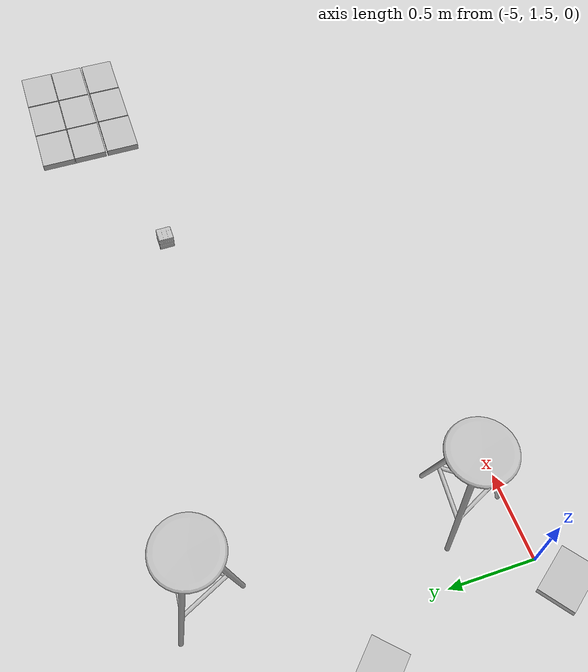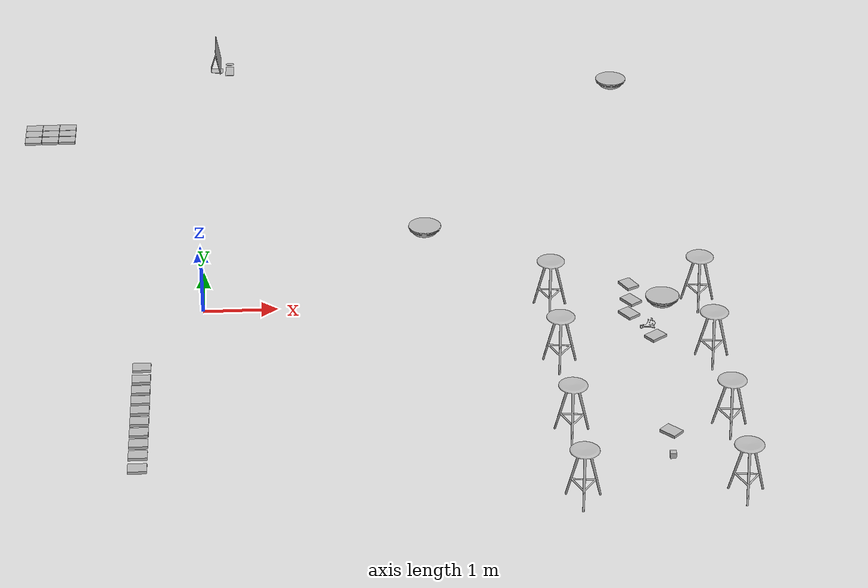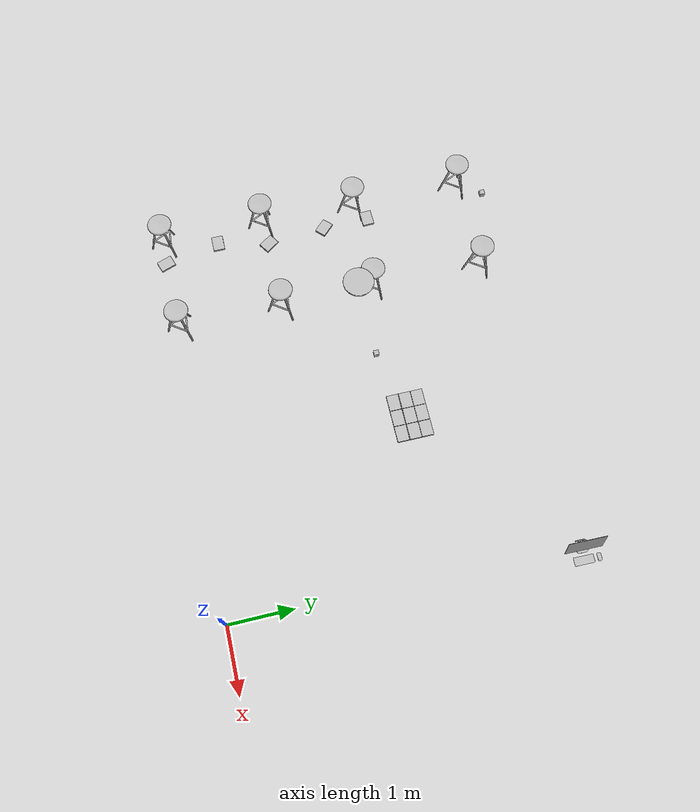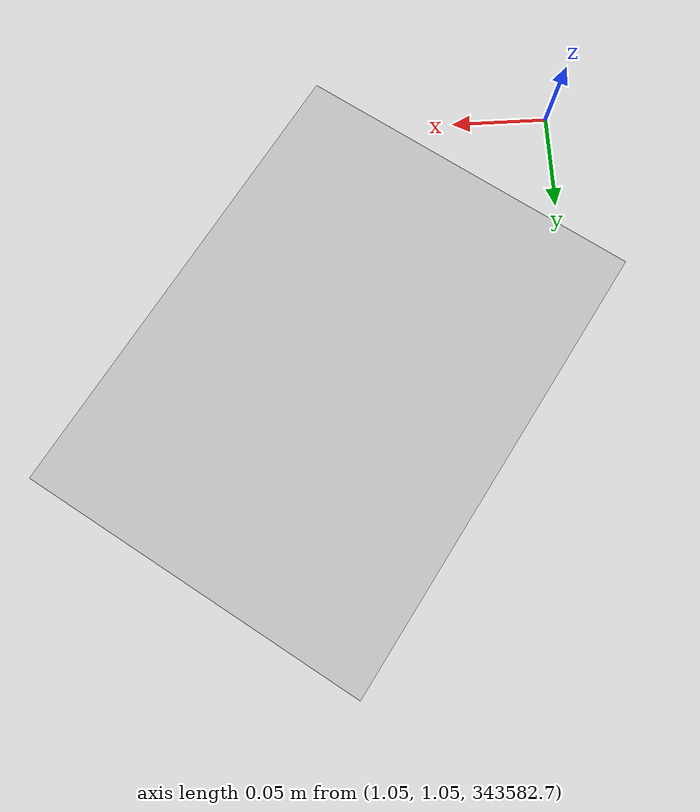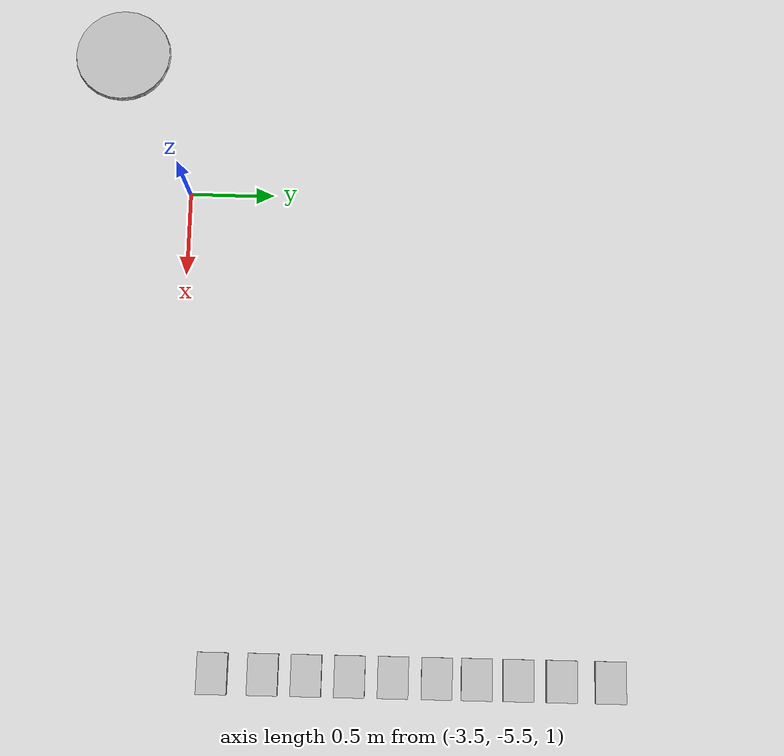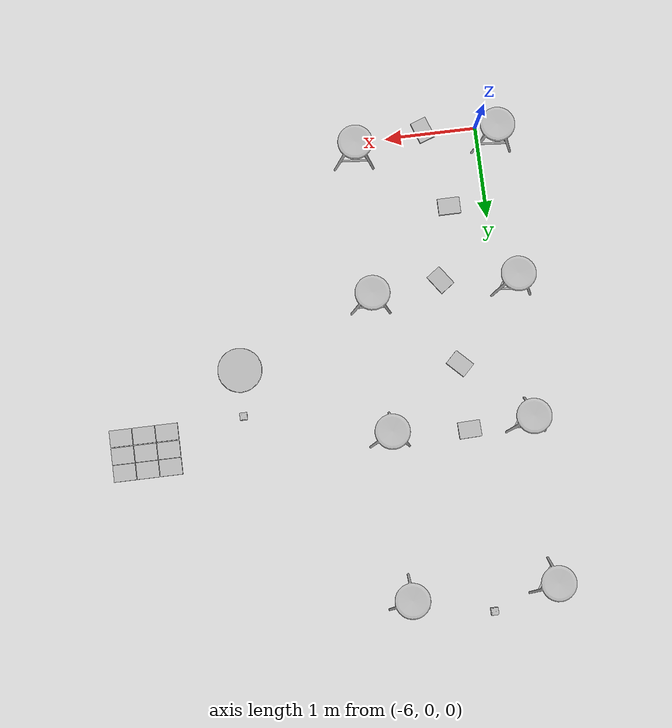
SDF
<sdf version="1.6">
 <world name="default">
  <gravity>0 0 -9.8</gravity>
  <magnetic_field>6e-06 2.3e-05 -4.2e-05</magnetic_field>
  <atmosphere type="adiabatic"/>
  <physics type="ode" name="rtu=1000,rtf=1,mss=0.001,iters=50" default="true">
   <real_time_update_rate>1000</real_time_update_rate>
   <real_time_factor>1</real_time_factor>
   <max_step_size>0.001</max_step_size>
   <ode><solver><type>quick</type><iters>50</iters></solver></ode>
  </physics>
  <physics type="ode" name="rtu=1000,rtf=1,mss=0.001,iters=25" default="false">
   <real_time_update_rate>1000</real_time_update_rate>
   <real_time_factor>1</real_time_factor>
   <max_step_size>0.001</max_step_size>
   <ode><solver><type>quick</type><iters>25</iters></solver></ode>
  </physics>
  <physics type="ode" name="rtu=1000,rtf=1,mss=0.001,iters=100" default="false">
   <real_time_update_rate>1000</real_time_update_rate>
   <real_time_factor>1</real_time_factor>
   <max_step_size>0.001</max_step_size>
   <ode><solver><type>quick</type><iters>100</iters></solver></ode>
  </physics>
  <physics type="ode" name="rtu=1000,rtf=1,mss=0.001,iters=200" default="false">
   <real_time_update_rate>1000</real_time_update_rate>
   <real_time_factor>1</real_time_factor>
   <max_step_size>0.001</max_step_size>
   <ode><solver><type>quick</type><iters>200</iters></solver></ode>
  </physics>
  <physics type="ode" name="rtu=1000,rtf=1,mss=0.0001,iters=50" default="false">
   <real_time_update_rate>1000</real_time_update_rate>
   <real_time_factor>1</real_time_factor>
   <max_step_size>0.0001</max_step_size>
   <ode><solver><type>quick</type><iters>50</iters></solver></ode>
  </physics>
  <physics type="ode" name="rtu=1000,rtf=1,mss=0.0001,iters=25" default="false">
   <real_time_update_rate>1000</real_time_update_rate>
   <real_time_factor>1</real_time_factor>
   <max_step_size>0.0001</max_step_size>
   <ode><solver><type>quick</type><iters>25</iters></solver></ode>
  </physics>
  <physics type="ode" name="rtu=1000,rtf=1,mss=0.0001,iters=100" default="false">
   <real_time_update_rate>1000</real_time_update_rate>
   <real_time_factor>1</real_time_factor>
   <max_step_size>0.0001</max_step_size>
   <ode><solver><type>quick</type><iters>100</iters></solver></ode>
  </physics>
  <physics type="ode" name="rtu=1000,rtf=1,mss=0.0001,iters=200" default="false">
   <real_time_update_rate>1000</real_time_update_rate>
   <real_time_factor>1</real_time_factor>
   <max_step_size>0.0001</max_step_size>
   <ode><solver><type>quick</type><iters>200</iters></solver></ode>
  </physics>
  <physics type="ode" name="rtu=1000,rtf=2,mss=0.001,iters=50" default="false">
   <real_time_update_rate>1000</real_time_update_rate>
   <real_time_factor>2</real_time_factor>
   <max_step_size>0.001</max_step_size>
   <ode><solver><type>quick</type><iters>50</iters></solver></ode>
  </physics>
  <physics type="ode" name="rtu=1000,rtf=2,mss=0.001,iters=25" default="false">
   <real_time_update_rate>1000</real_time_update_rate>
   <real_time_factor>2</real_time_factor>
   <max_step_size>0.001</max_step_size>
   <ode><solver><type>quick</type><iters>25</iters></solver></ode>
  </physics>
  <physics type="ode" name="rtu=1000,rtf=2,mss=0.001,iters=100" default="false">
   <real_time_update_rate>1000</real_time_update_rate>
   <real_time_factor>2</real_time_factor>
   <max_step_size>0.001</max_step_size>
   <ode><solver><type>quick</type><iters>100</iters></solver></ode>
  </physics>
  <physics type="ode" name="rtu=1000,rtf=2,mss=0.001,iters=200" default="false">
   <real_time_update_rate>1000</real_time_update_rate>
   <real_time_factor>2</real_time_factor>
   <max_step_size>0.001</max_step_size>
   <ode><solver><type>quick</type><iters>200</iters></solver></ode>
  </physics>
  <physics type="ode" name="rtu=1000,rtf=2,mss=0.0001,iters=50" default="false">
   <real_time_update_rate>1000</real_time_update_rate>
   <real_time_factor>2</real_time_factor>
   <max_step_size>0.0001</max_step_size>
   <ode><solver><type>quick</type><iters>50</iters></solver></ode>
  </physics>
  <physics type="ode" name="rtu=1000,rtf=2,mss=0.0001,iters=25" default="false">
   <real_time_update_rate>1000</real_time_update_rate>
   <real_time_factor>2</real_time_factor>
   <max_step_size>0.0001</max_step_size>
   <ode><solver><type>quick</type><iters>25</iters></solver></ode>
  </physics>
  <physics type="ode" name="rtu=1000,rtf=2,mss=0.0001,iters=100" default="false">
   <real_time_update_rate>1000</real_time_update_rate>
   <real_time_factor>2</real_time_factor>
   <max_step_size>0.0001</max_step_size>
   <ode><solver><type>quick</type><iters>100</iters></solver></ode>
  </physics>
  <physics type="ode" name="rtu=1000,rtf=2,mss=0.0001,iters=200" default="false">
   <real_time_update_rate>1000</real_time_update_rate>
   <real_time_factor>2</real_time_factor>
   <max_step_size>0.0001</max_step_size>
   <ode><solver><type>quick</type><iters>200</iters></solver></ode>
  </physics>
  <physics type="ode" name="rtu=1000,rtf=5,mss=0.001,iters=50" default="false">
   <real_time_update_rate>1000</real_time_update_rate>
   <real_time_factor>5</real_time_factor>
   <max_step_size>0.001</max_step_size>
   <ode><solver><type>quick</type><iters>50</iters></solver></ode>
  </physics>
  <physics type="ode" name="rtu=1000,rtf=5,mss=0.001,iters=25" default="false">
   <real_time_update_rate>1000</real_time_update_rate>
   <real_time_factor>5</real_time_factor>
   <max_step_size>0.001</max_step_size>
   <ode><solver><type>quick</type><iters>25</iters></solver></ode>
  </physics>
  <physics type="ode" name="rtu=1000,rtf=5,mss=0.001,iters=100" default="false">
   <real_time_update_rate>1000</real_time_update_rate>
   <real_time_factor>5</real_time_factor>
   <max_step_size>0.001</max_step_size>
   <ode><solver><type>quick</type><iters>100</iters></solver></ode>
  </physics>
  <physics type="ode" name="rtu=1000,rtf=5,mss=0.001,iters=200" default="false">
   <real_time_update_rate>1000</real_time_update_rate>
   <real_time_factor>5</real_time_factor>
   <max_step_size>0.001</max_step_size>
   <ode><solver><type>quick</type><iters>200</iters></solver></ode>
  </physics>
  <physics type="ode" name="rtu=1000,rtf=5,mss=0.0001,iters=50" default="false">
   <real_time_update_rate>1000</real_time_update_rate>
   <real_time_factor>5</real_time_factor>
   <max_step_size>0.0001</max_step_size>
   <ode><solver><type>quick</type><iters>50</iters></solver></ode>
  </physics>
  <physics type="ode" name="rtu=1000,rtf=5,mss=0.0001,iters=25" default="false">
   <real_time_update_rate>1000</real_time_update_rate>
   <real_time_factor>5</real_time_factor>
   <max_step_size>0.0001</max_step_size>
   <ode><solver><type>quick</type><iters>25</iters></solver></ode>
  </physics>
  <physics type="ode" name="rtu=1000,rtf=5,mss=0.0001,iters=100" default="false">
   <real_time_update_rate>1000</real_time_update_rate>
   <real_time_factor>5</real_time_factor>
   <max_step_size>0.0001</max_step_size>
   <ode><solver><type>quick</type><iters>100</iters></solver></ode>
  </physics>
  <physics type="ode" name="rtu=1000,rtf=5,mss=0.0001,iters=200" default="false">
   <real_time_update_rate>1000</real_time_update_rate>
   <real_time_factor>5</real_time_factor>
   <max_step_size>0.0001</max_step_size>
   <ode><solver><type>quick</type><iters>200</iters></solver></ode>
  </physics>
  <physics type="ode" name="rtu=1000,rtf=10,mss=0.001,iters=50" default="false">
   <real_time_update_rate>1000</real_time_update_rate>
   <real_time_factor>10</real_time_factor>
   <max_step_size>0.001</max_step_size>
   <ode><solver><type>quick</type><iters>50</iters></solver></ode>
  </physics>
  <physics type="ode" name="rtu=1000,rtf=10,mss=0.001,iters=25" default="false">
   <real_time_update_rate>1000</real_time_update_rate>
   <real_time_factor>10</real_time_factor>
   <max_step_size>0.001</max_step_size>
   <ode><solver><type>quick</type><iters>25</iters></solver></ode>
  </physics>
  <physics type="ode" name="rtu=1000,rtf=10,mss=0.001,iters=100" default="false">
   <real_time_update_rate>1000</real_time_update_rate>
   <real_time_factor>10</real_time_factor>
   <max_step_size>0.001</max_step_size>
   <ode><solver><type>quick</type><iters>100</iters></solver></ode>
  </physics>
  <physics type="ode" name="rtu=1000,rtf=10,mss=0.001,iters=200" default="false">
   <real_time_update_rate>1000</real_time_update_rate>
   <real_time_factor>10</real_time_factor>
   <max_step_size>0.001</max_step_size>
   <ode><solver><type>quick</type><iters>200</iters></solver></ode>
  </physics>
  <physics type="ode" name="rtu=1000,rtf=10,mss=0.0001,iters=50" default="false">
   <real_time_update_rate>1000</real_time_update_rate>
   <real_time_factor>10</real_time_factor>
   <max_step_size>0.0001</max_step_size>
   <ode><solver><type>quick</type><iters>50</iters></solver></ode>
  </physics>
  <physics type="ode" name="rtu=1000,rtf=10,mss=0.0001,iters=25" default="false">
   <real_time_update_rate>1000</real_time_update_rate>
   <real_time_factor>10</real_time_factor>
   <max_step_size>0.0001</max_step_size>
   <ode><solver><type>quick</type><iters>25</iters></solver></ode>
  </physics>
  <physics type="ode" name="rtu=1000,rtf=10,mss=0.0001,iters=100" default="false">
   <real_time_update_rate>1000</real_time_update_rate>
   <real_time_factor>10</real_time_factor>
   <max_step_size>0.0001</max_step_size>
   <ode><solver><type>quick</type><iters>100</iters></solver></ode>
  </physics>
  <physics type="ode" name="rtu=1000,rtf=10,mss=0.0001,iters=200" default="false">
   <real_time_update_rate>1000</real_time_update_rate>
   <real_time_factor>10</real_time_factor>
   <max_step_size>0.0001</max_step_size>
   <ode><solver><type>quick</type><iters>200</iters></solver></ode>
  </physics>
  <physics type="ode" name="rtu=1000,rtf=20,mss=0.001,iters=50" default="false">
   <real_time_update_rate>1000</real_time_update_rate>
   <real_time_factor>20</real_time_factor>
   <max_step_size>0.001</max_step_size>
   <ode><solver><type>quick</type><iters>50</iters></solver></ode>
  </physics>
  <physics type="ode" name="rtu=1000,rtf=20,mss=0.001,iters=25" default="false">
   <real_time_update_rate>1000</real_time_update_rate>
   <real_time_factor>20</real_time_factor>
   <max_step_size>0.001</max_step_size>
   <ode><solver><type>quick</type><iters>25</iters></solver></ode>
  </physics>
  <physics type="ode" name="rtu=1000,rtf=20,mss=0.001,iters=100" default="false">
   <real_time_update_rate>1000</real_time_update_rate>
   <real_time_factor>20</real_time_factor>
   <max_step_size>0.001</max_step_size>
   <ode><solver><type>quick</type><iters>100</iters></solver></ode>
  </physics>
  <physics type="ode" name="rtu=1000,rtf=20,mss=0.001,iters=200" default="false">
   <real_time_update_rate>1000</real_time_update_rate>
   <real_time_factor>20</real_time_factor>
   <max_step_size>0.001</max_step_size>
   <ode><solver><type>quick</type><iters>200</iters></solver></ode>
  </physics>
  <physics type="ode" name="rtu=1000,rtf=20,mss=0.0001,iters=50" default="false">
   <real_time_update_rate>1000</real_time_update_rate>
   <real_time_factor>20</real_time_factor>
   <max_step_size>0.0001</max_step_size>
   <ode><solver><type>quick</type><iters>50</iters></solver></ode>
  </physics>
  <physics type="ode" name="rtu=1000,rtf=20,mss=0.0001,iters=25" default="false">
   <real_time_update_rate>1000</real_time_update_rate>
   <real_time_factor>20</real_time_factor>
   <max_step_size>0.0001</max_step_size>
   <ode><solver><type>quick</type><iters>25</iters></solver></ode>
  </physics>
  <physics type="ode" name="rtu=1000,rtf=20,mss=0.0001,iters=100" default="false">
   <real_time_update_rate>1000</real_time_update_rate>
   <real_time_factor>20</real_time_factor>
   <max_step_size>0.0001</max_step_size>
   <ode><solver><type>quick</type><iters>100</iters></solver></ode>
  </physics>
  <physics type="ode" name="rtu=1000,rtf=20,mss=0.0001,iters=200" default="false">
   <real_time_update_rate>1000</real_time_update_rate>
   <real_time_factor>20</real_time_factor>
   <max_step_size>0.0001</max_step_size>
   <ode><solver><type>quick</type><iters>200</iters></solver></ode>
  </physics>
  <physics type="ode" name="rtu=2000,rtf=1,mss=0.001,iters=50" default="false">
   <real_time_update_rate>2000</real_time_update_rate>
   <real_time_factor>1</real_time_factor>
   <max_step_size>0.001</max_step_size>
   <ode><solver><type>quick</type><iters>50</iters></solver></ode>
  </physics>
  <physics type="ode" name="rtu=2000,rtf=1,mss=0.001,iters=25" default="false">
   <real_time_update_rate>2000</real_time_update_rate>
   <real_time_factor>1</real_time_factor>
   <max_step_size>0.001</max_step_size>
   <ode><solver><type>quick</type><iters>25</iters></solver></ode>
  </physics>
  <physics type="ode" name="rtu=2000,rtf=1,mss=0.001,iters=100" default="false">
   <real_time_update_rate>2000</real_time_update_rate>
   <real_time_factor>1</real_time_factor>
   <max_step_size>0.001</max_step_size>
   <ode><solver><type>quick</type><iters>100</iters></solver></ode>
  </physics>
  <physics type="ode" name="rtu=2000,rtf=1,mss=0.001,iters=200" default="false">
   <real_time_update_rate>2000</real_time_update_rate>
   <real_time_factor>1</real_time_factor>
   <max_step_size>0.001</max_step_size>
   <ode><solver><type>quick</type><iters>200</iters></solver></ode>
  </physics>
  <physics type="ode" name="rtu=2000,rtf=1,mss=0.0001,iters=50" default="false">
   <real_time_update_rate>2000</real_time_update_rate>
   <real_time_factor>1</real_time_factor>
   <max_step_size>0.0001</max_step_size>
   <ode><solver><type>quick</type><iters>50</iters></solver></ode>
  </physics>
  <physics type="ode" name="rtu=2000,rtf=1,mss=0.0001,iters=25" default="false">
   <real_time_update_rate>2000</real_time_update_rate>
   <real_time_factor>1</real_time_factor>
   <max_step_size>0.0001</max_step_size>
   <ode><solver><type>quick</type><iters>25</iters></solver></ode>
  </physics>
  <physics type="ode" name="rtu=2000,rtf=1,mss=0.0001,iters=100" default="false">
   <real_time_update_rate>2000</real_time_update_rate>
   <real_time_factor>1</real_time_factor>
   <max_step_size>0.0001</max_step_size>
   <ode><solver><type>quick</type><iters>100</iters></solver></ode>
  </physics>
  <physics type="ode" name="rtu=2000,rtf=1,mss=0.0001,iters=200" default="false">
   <real_time_update_rate>2000</real_time_update_rate>
   <real_time_factor>1</real_time_factor>
   <max_step_size>0.0001</max_step_size>
   <ode><solver><type>quick</type><iters>200</iters></solver></ode>
  </physics>
  <physics type="ode" name="rtu=2000,rtf=2,mss=0.001,iters=50" default="false">
   <real_time_update_rate>2000</real_time_update_rate>
   <real_time_factor>2</real_time_factor>
   <max_step_size>0.001</max_step_size>
   <ode><solver><type>quick</type><iters>50</iters></solver></ode>
  </physics>
  <physics type="ode" name="rtu=2000,rtf=2,mss=0.001,iters=25" default="false">
   <real_time_update_rate>2000</real_time_update_rate>
   <real_time_factor>2</real_time_factor>
   <max_step_size>0.001</max_step_size>
   <ode><solver><type>quick</type><iters>25</iters></solver></ode>
  </physics>
  <physics type="ode" name="rtu=2000,rtf=2,mss=0.001,iters=100" default="false">
   <real_time_update_rate>2000</real_time_update_rate>
   <real_time_factor>2</real_time_factor>
   <max_step_size>0.001</max_step_size>
   <ode><solver><type>quick</type><iters>100</iters></solver></ode>
  </physics>
  <physics type="ode" name="rtu=2000,rtf=2,mss=0.001,iters=200" default="false">
   <real_time_update_rate>2000</real_time_update_rate>
   <real_time_factor>2</real_time_factor>
   <max_step_size>0.001</max_step_size>
   <ode><solver><type>quick</type><iters>200</iters></solver></ode>
  </physics>
  <physics type="ode" name="rtu=2000,rtf=2,mss=0.0001,iters=50" default="false">
   <real_time_update_rate>2000</real_time_update_rate>
   <real_time_factor>2</real_time_factor>
   <max_step_size>0.0001</max_step_size>
   <ode><solver><type>quick</type><iters>50</iters></solver></ode>
  </physics>
  <physics type="ode" name="rtu=2000,rtf=2,mss=0.0001,iters=25" default="false">
   <real_time_update_rate>2000</real_time_update_rate>
   <real_time_factor>2</real_time_factor>
   <max_step_size>0.0001</max_step_size>
   <ode><solver><type>quick</type><iters>25</iters></solver></ode>
  </physics>
  <physics type="ode" name="rtu=2000,rtf=2,mss=0.0001,iters=100" default="false">
   <real_time_update_rate>2000</real_time_update_rate>
   <real_time_factor>2</real_time_factor>
   <max_step_size>0.0001</max_step_size>
   <ode><solver><type>quick</type><iters>100</iters></solver></ode>
  </physics>
  <physics type="ode" name="rtu=2000,rtf=2,mss=0.0001,iters=200" default="false">
   <real_time_update_rate>2000</real_time_update_rate>
   <real_time_factor>2</real_time_factor>
   <max_step_size>0.0001</max_step_size>
   <ode><solver><type>quick</type><iters>200</iters></solver></ode>
  </physics>
  <physics type="ode" name="rtu=2000,rtf=5,mss=0.001,iters=50" default="false">
   <real_time_update_rate>2000</real_time_update_rate>
   <real_time_factor>5</real_time_factor>
   <max_step_size>0.001</max_step_size>
   <ode><solver><type>quick</type><iters>50</iters></solver></ode>
  </physics>
  <physics type="ode" name="rtu=2000,rtf=5,mss=0.001,iters=25" default="false">
   <real_time_update_rate>2000</real_time_update_rate>
   <real_time_factor>5</real_time_factor>
   <max_step_size>0.001</max_step_size>
   <ode><solver><type>quick</type><iters>25</iters></solver></ode>
  </physics>
  <physics type="ode" name="rtu=2000,rtf=5,mss=0.001,iters=100" default="false">
   <real_time_update_rate>2000</real_time_update_rate>
   <real_time_factor>5</real_time_factor>
   <max_step_size>0.001</max_step_size>
   <ode><solver><type>quick</type><iters>100</iters></solver></ode>
  </physics>
  <physics type="ode" name="rtu=2000,rtf=5,mss=0.001,iters=200" default="false">
   <real_time_update_rate>2000</real_time_update_rate>
   <real_time_factor>5</real_time_factor>
   <max_step_size>0.001</max_step_size>
   <ode><solver><type>quick</type><iters>200</iters></solver></ode>
  </physics>
  <physics type="ode" name="rtu=2000,rtf=5,mss=0.0001,iters=50" default="false">
   <real_time_update_rate>2000</real_time_update_rate>
   <real_time_factor>5</real_time_factor>
   <max_step_size>0.0001</max_step_size>
   <ode><solver><type>quick</type><iters>50</iters></solver></ode>
  </physics>
  <physics type="ode" name="rtu=2000,rtf=5,mss=0.0001,iters=25" default="false">
   <real_time_update_rate>2000</real_time_update_rate>
   <real_time_factor>5</real_time_factor>
   <max_step_size>0.0001</max_step_size>
   <ode><solver><type>quick</type><iters>25</iters></solver></ode>
  </physics>
  <physics type="ode" name="rtu=2000,rtf=5,mss=0.0001,iters=100" default="false">
   <real_time_update_rate>2000</real_time_update_rate>
   <real_time_factor>5</real_time_factor>
   <max_step_size>0.0001</max_step_size>
   <ode><solver><type>quick</type><iters>100</iters></solver></ode>
  </physics>
  <physics type="ode" name="rtu=2000,rtf=5,mss=0.0001,iters=200" default="false">
   <real_time_update_rate>2000</real_time_update_rate>
   <real_time_factor>5</real_time_factor>
   <max_step_size>0.0001</max_step_size>
   <ode><solver><type>quick</type><iters>200</iters></solver></ode>
  </physics>
  <physics type="ode" name="rtu=2000,rtf=10,mss=0.001,iters=50" default="false">
   <real_time_update_rate>2000</real_time_update_rate>
   <real_time_factor>10</real_time_factor>
   <max_step_size>0.001</max_step_size>
   <ode><solver><type>quick</type><iters>50</iters></solver></ode>
  </physics>
  <physics type="ode" name="rtu=2000,rtf=10,mss=0.001,iters=25" default="false">
   <real_time_update_rate>2000</real_time_update_rate>
   <real_time_factor>10</real_time_factor>
   <max_step_size>0.001</max_step_size>
   <ode><solver><type>quick</type><iters>25</iters></solver></ode>
  </physics>
  <physics type="ode" name="rtu=2000,rtf=10,mss=0.001,iters=100" default="false">
   <real_time_update_rate>2000</real_time_update_rate>
   <real_time_factor>10</real_time_factor>
   <max_step_size>0.001</max_step_size>
   <ode><solver><type>quick</type><iters>100</iters></solver></ode>
  </physics>
  <physics type="ode" name="rtu=2000,rtf=10,mss=0.001,iters=200" default="false">
   <real_time_update_rate>2000</real_time_update_rate>
   <real_time_factor>10</real_time_factor>
   <max_step_size>0.001</max_step_size>
   <ode><solver><type>quick</type><iters>200</iters></solver></ode>
  </physics>
  <physics type="ode" name="rtu=2000,rtf=10,mss=0.0001,iters=50" default="false">
   <real_time_update_rate>2000</real_time_update_rate>
   <real_time_factor>10</real_time_factor>
   <max_step_size>0.0001</max_step_size>
   <ode><solver><type>quick</type><iters>50</iters></solver></ode>
  </physics>
  <physics type="ode" name="rtu=2000,rtf=10,mss=0.0001,iters=25" default="false">
   <real_time_update_rate>2000</real_time_update_rate>
   <real_time_factor>10</real_time_factor>
   <max_step_size>0.0001</max_step_size>
   <ode><solver><type>quick</type><iters>25</iters></solver></ode>
  </physics>
  <physics type="ode" name="rtu=2000,rtf=10,mss=0.0001,iters=100" default="false">
   <real_time_update_rate>2000</real_time_update_rate>
   <real_time_factor>10</real_time_factor>
   <max_step_size>0.0001</max_step_size>
   <ode><solver><type>quick</type><iters>100</iters></solver></ode>
  </physics>
  <physics type="ode" name="rtu=2000,rtf=10,mss=0.0001,iters=200" default="false">
   <real_time_update_rate>2000</real_time_update_rate>
   <real_time_factor>10</real_time_factor>
   <max_step_size>0.0001</max_step_size>
   <ode><solver><type>quick</type><iters>200</iters></solver></ode>
  </physics>
  <physics type="ode" name="rtu=2000,rtf=20,mss=0.001,iters=50" default="false">
   <real_time_update_rate>2000</real_time_update_rate>
   <real_time_factor>20</real_time_factor>
   <max_step_size>0.001</max_step_size>
   <ode><solver><type>quick</type><iters>50</iters></solver></ode>
  </physics>
  <physics type="ode" name="rtu=2000,rtf=20,mss=0.001,iters=25" default="false">
   <real_time_update_rate>2000</real_time_update_rate>
   <real_time_factor>20</real_time_factor>
   <max_step_size>0.001</max_step_size>
   <ode><solver><type>quick</type><iters>25</iters></solver></ode>
  </physics>
  <physics type="ode" name="rtu=2000,rtf=20,mss=0.001,iters=100" default="false">
   <real_time_update_rate>2000</real_time_update_rate>
   <real_time_factor>20</real_time_factor>
   <max_step_size>0.001</max_step_size>
   <ode><solver><type>quick</type><iters>100</iters></solver></ode>
  </physics>
  <physics type="ode" name="rtu=2000,rtf=20,mss=0.001,iters=200" default="false">
   <real_time_update_rate>2000</real_time_update_rate>
   <real_time_factor>20</real_time_factor>
   <max_step_size>0.001</max_step_size>
   <ode><solver><type>quick</type><iters>200</iters></solver></ode>
  </physics>
  <physics type="ode" name="rtu=2000,rtf=20,mss=0.0001,iters=50" default="false">
   <real_time_update_rate>2000</real_time_update_rate>
   <real_time_factor>20</real_time_factor>
   <max_step_size>0.0001</max_step_size>
   <ode><solver><type>quick</type><iters>50</iters></solver></ode>
  </physics>
  <physics type="ode" name="rtu=2000,rtf=20,mss=0.0001,iters=25" default="false">
   <real_time_update_rate>2000</real_time_update_rate>
   <real_time_factor>20</real_time_factor>
   <max_step_size>0.0001</max_step_size>
   <ode><solver><type>quick</type><iters>25</iters></solver></ode>
  </physics>
  <physics type="ode" name="rtu=2000,rtf=20,mss=0.0001,iters=100" default="false">
   <real_time_update_rate>2000</real_time_update_rate>
   <real_time_factor>20</real_time_factor>
   <max_step_size>0.0001</max_step_size>
   <ode><solver><type>quick</type><iters>100</iters></solver></ode>
  </physics>
  <physics type="ode" name="rtu=2000,rtf=20,mss=0.0001,iters=200" default="false">
   <real_time_update_rate>2000</real_time_update_rate>
   <real_time_factor>20</real_time_factor>
   <max_step_size>0.0001</max_step_size>
   <ode><solver><type>quick</type><iters>200</iters></solver></ode>
  </physics>
  <physics type="ode" name="rtu=5000,rtf=1,mss=0.001,iters=50" default="false">
   <real_time_update_rate>5000</real_time_update_rate>
   <real_time_factor>1</real_time_factor>
   <max_step_size>0.001</max_step_size>
   <ode><solver><type>quick</type><iters>50</iters></solver></ode>
  </physics>
  <physics type="ode" name="rtu=5000,rtf=1,mss=0.001,iters=25" default="false">
   <real_time_update_rate>5000</real_time_update_rate>
   <real_time_factor>1</real_time_factor>
   <max_step_size>0.001</max_step_size>
   <ode><solver><type>quick</type><iters>25</iters></solver></ode>
  </physics>
  <physics type="ode" name="rtu=5000,rtf=1,mss=0.001,iters=100" default="false">
   <real_time_update_rate>5000</real_time_update_rate>
   <real_time_factor>1</real_time_factor>
   <max_step_size>0.001</max_step_size>
   <ode><solver><type>quick</type><iters>100</iters></solver></ode>
  </physics>
  <physics type="ode" name="rtu=5000,rtf=1,mss=0.001,iters=200" default="false">
   <real_time_update_rate>5000</real_time_update_rate>
   <real_time_factor>1</real_time_factor>
   <max_step_size>0.001</max_step_size>
   <ode><solver><type>quick</type><iters>200</iters></solver></ode>
  </physics>
  <physics type="ode" name="rtu=5000,rtf=1,mss=0.0001,iters=50" default="false">
   <real_time_update_rate>5000</real_time_update_rate>
   <real_time_factor>1</real_time_factor>
   <max_step_size>0.0001</max_step_size>
   <ode><solver><type>quick</type><iters>50</iters></solver></ode>
  </physics>
  <physics type="ode" name="rtu=5000,rtf=1,mss=0.0001,iters=25" default="false">
   <real_time_update_rate>5000</real_time_update_rate>
   <real_time_factor>1</real_time_factor>
   <max_step_size>0.0001</max_step_size>
   <ode><solver><type>quick</type><iters>25</iters></solver></ode>
  </physics>
  <physics type="ode" name="rtu=5000,rtf=1,mss=0.0001,iters=100" default="false">
   <real_time_update_rate>5000</real_time_update_rate>
   <real_time_factor>1</real_time_factor>
   <max_step_size>0.0001</max_step_size>
   <ode><solver><type>quick</type><iters>100</iters></solver></ode>
  </physics>
  <physics type="ode" name="rtu=5000,rtf=1,mss=0.0001,iters=200" default="false">
   <real_time_update_rate>5000</real_time_update_rate>
   <real_time_factor>1</real_time_factor>
   <max_step_size>0.0001</max_step_size>
   <ode><solver><type>quick</type><iters>200</iters></solver></ode>
  </physics>
  <physics type="ode" name="rtu=5000,rtf=2,mss=0.001,iters=50" default="false">
   <real_time_update_rate>5000</real_time_update_rate>
   <real_time_factor>2</real_time_factor>
   <max_step_size>0.001</max_step_size>
   <ode><solver><type>quick</type><iters>50</iters></solver></ode>
  </physics>
  <physics type="ode" name="rtu=5000,rtf=2,mss=0.001,iters=25" default="false">
   <real_time_update_rate>5000</real_time_update_rate>
   <real_time_factor>2</real_time_factor>
   <max_step_size>0.001</max_step_size>
   <ode><solver><type>quick</type><iters>25</iters></solver></ode>
  </physics>
  <physics type="ode" name="rtu=5000,rtf=2,mss=0.001,iters=100" default="false">
   <real_time_update_rate>5000</real_time_update_rate>
   <real_time_factor>2</real_time_factor>
   <max_step_size>0.001</max_step_size>
   <ode><solver><type>quick</type><iters>100</iters></solver></ode>
  </physics>
  <physics type="ode" name="rtu=5000,rtf=2,mss=0.001,iters=200" default="false">
   <real_time_update_rate>5000</real_time_update_rate>
   <real_time_factor>2</real_time_factor>
   <max_step_size>0.001</max_step_size>
   <ode><solver><type>quick</type><iters>200</iters></solver></ode>
  </physics>
  <physics type="ode" name="rtu=5000,rtf=2,mss=0.0001,iters=50" default="false">
   <real_time_update_rate>5000</real_time_update_rate>
   <real_time_factor>2</real_time_factor>
   <max_step_size>0.0001</max_step_size>
   <ode><solver><type>quick</type><iters>50</iters></solver></ode>
  </physics>
  <physics type="ode" name="rtu=5000,rtf=2,mss=0.0001,iters=25" default="false">
   <real_time_update_rate>5000</real_time_update_rate>
   <real_time_factor>2</real_time_factor>
   <max_step_size>0.0001</max_step_size>
   <ode><solver><type>quick</type><iters>25</iters></solver></ode>
  </physics>
  <physics type="ode" name="rtu=5000,rtf=2,mss=0.0001,iters=100" default="false">
   <real_time_update_rate>5000</real_time_update_rate>
   <real_time_factor>2</real_time_factor>
   <max_step_size>0.0001</max_step_size>
   <ode><solver><type>quick</type><iters>100</iters></solver></ode>
  </physics>
  <physics type="ode" name="rtu=5000,rtf=2,mss=0.0001,iters=200" default="false">
   <real_time_update_rate>5000</real_time_update_rate>
   <real_time_factor>2</real_time_factor>
   <max_step_size>0.0001</max_step_size>
   <ode><solver><type>quick</type><iters>200</iters></solver></ode>
  </physics>
  <physics type="ode" name="rtu=5000,rtf=5,mss=0.001,iters=50" default="false">
   <real_time_update_rate>5000</real_time_update_rate>
   <real_time_factor>5</real_time_factor>
   <max_step_size>0.001</max_step_size>
   <ode><solver><type>quick</type><iters>50</iters></solver></ode>
  </physics>
  <physics type="ode" name="rtu=5000,rtf=5,mss=0.001,iters=25" default="false">
   <real_time_update_rate>5000</real_time_update_rate>
   <real_time_factor>5</real_time_factor>
   <max_step_size>0.001</max_step_size>
   <ode><solver><type>quick</type><iters>25</iters></solver></ode>
  </physics>
  <physics type="ode" name="rtu=5000,rtf=5,mss=0.001,iters=100" default="false">
   <real_time_update_rate>5000</real_time_update_rate>
   <real_time_factor>5</real_time_factor>
   <max_step_size>0.001</max_step_size>
   <ode><solver><type>quick</type><iters>100</iters></solver></ode>
  </physics>
  <physics type="ode" name="rtu=5000,rtf=5,mss=0.001,iters=200" default="false">
   <real_time_update_rate>5000</real_time_update_rate>
   <real_time_factor>5</real_time_factor>
   <max_step_size>0.001</max_step_size>
   <ode><solver><type>quick</type><iters>200</iters></solver></ode>
  </physics>
  <physics type="ode" name="rtu=5000,rtf=5,mss=0.0001,iters=50" default="false">
   <real_time_update_rate>5000</real_time_update_rate>
   <real_time_factor>5</real_time_factor>
   <max_step_size>0.0001</max_step_size>
   <ode><solver><type>quick</type><iters>50</iters></solver></ode>
  </physics>
  <physics type="ode" name="rtu=5000,rtf=5,mss=0.0001,iters=25" default="false">
   <real_time_update_rate>5000</real_time_update_rate>
   <real_time_factor>5</real_time_factor>
   <max_step_size>0.0001</max_step_size>
   <ode><solver><type>quick</type><iters>25</iters></solver></ode>
  </physics>
  <physics type="ode" name="rtu=5000,rtf=5,mss=0.0001,iters=100" default="false">
   <real_time_update_rate>5000</real_time_update_rate>
   <real_time_factor>5</real_time_factor>
   <max_step_size>0.0001</max_step_size>
   <ode><solver><type>quick</type><iters>100</iters></solver></ode>
  </physics>
  <physics type="ode" name="rtu=5000,rtf=5,mss=0.0001,iters=200" default="false">
   <real_time_update_rate>5000</real_time_update_rate>
   <real_time_factor>5</real_time_factor>
   <max_step_size>0.0001</max_step_size>
   <ode><solver><type>quick</type><iters>200</iters></solver></ode>
  </physics>
  <physics type="ode" name="rtu=5000,rtf=10,mss=0.001,iters=50" default="false">
   <real_time_update_rate>5000</real_time_update_rate>
   <real_time_factor>10</real_time_factor>
   <max_step_size>0.001</max_step_size>
   <ode><solver><type>quick</type><iters>50</iters></solver></ode>
  </physics>
  <physics type="ode" name="rtu=5000,rtf=10,mss=0.001,iters=25" default="false">
   <real_time_update_rate>5000</real_time_update_rate>
   <real_time_factor>10</real_time_factor>
   <max_step_size>0.001</max_step_size>
   <ode><solver><type>quick</type><iters>25</iters></solver></ode>
  </physics>
  <physics type="ode" name="rtu=5000,rtf=10,mss=0.001,iters=100" default="false">
   <real_time_update_rate>5000</real_time_update_rate>
   <real_time_factor>10</real_time_factor>
   <max_step_size>0.001</max_step_size>
   <ode><solver><type>quick</type><iters>100</iters></solver></ode>
  </physics>
  <physics type="ode" name="rtu=5000,rtf=10,mss=0.001,iters=200" default="false">
   <real_time_update_rate>5000</real_time_update_rate>
   <real_time_factor>10</real_time_factor>
   <max_step_size>0.001</max_step_size>
   <ode><solver><type>quick</type><iters>200</iters></solver></ode>
  </physics>
  <physics type="ode" name="rtu=5000,rtf=10,mss=0.0001,iters=50" default="false">
   <real_time_update_rate>5000</real_time_update_rate>
   <real_time_factor>10</real_time_factor>
   <max_step_size>0.0001</max_step_size>
   <ode><solver><type>quick</type><iters>50</iters></solver></ode>
  </physics>
  <physics type="ode" name="rtu=5000,rtf=10,mss=0.0001,iters=25" default="false">
   <real_time_update_rate>5000</real_time_update_rate>
   <real_time_factor>10</real_time_factor>
   <max_step_size>0.0001</max_step_size>
   <ode><solver><type>quick</type><iters>25</iters></solver></ode>
  </physics>
  <physics type="ode" name="rtu=5000,rtf=10,mss=0.0001,iters=100" default="false">
   <real_time_update_rate>5000</real_time_update_rate>
   <real_time_factor>10</real_time_factor>
   <max_step_size>0.0001</max_step_size>
   <ode><solver><type>quick</type><iters>100</iters></solver></ode>
  </physics>
  <physics type="ode" name="rtu=5000,rtf=10,mss=0.0001,iters=200" default="false">
   <real_time_update_rate>5000</real_time_update_rate>
   <real_time_factor>10</real_time_factor>
   <max_step_size>0.0001</max_step_size>
   <ode><solver><type>quick</type><iters>200</iters></solver></ode>
  </physics>
  <physics type="ode" name="rtu=5000,rtf=20,mss=0.001,iters=50" default="false">
   <real_time_update_rate>5000</real_time_update_rate>
   <real_time_factor>20</real_time_factor>
   <max_step_size>0.001</max_step_size>
   <ode><solver><type>quick</type><iters>50</iters></solver></ode>
  </physics>
  <physics type="ode" name="rtu=5000,rtf=20,mss=0.001,iters=25" default="false">
   <real_time_update_rate>5000</real_time_update_rate>
   <real_time_factor>20</real_time_factor>
   <max_step_size>0.001</max_step_size>
   <ode><solver><type>quick</type><iters>25</iters></solver></ode>
  </physics>
  <physics type="ode" name="rtu=5000,rtf=20,mss=0.001,iters=100" default="false">
   <real_time_update_rate>5000</real_time_update_rate>
   <real_time_factor>20</real_time_factor>
   <max_step_size>0.001</max_step_size>
   <ode><solver><type>quick</type><iters>100</iters></solver></ode>
  </physics>
  <physics type="ode" name="rtu=5000,rtf=20,mss=0.001,iters=200" default="false">
   <real_time_update_rate>5000</real_time_update_rate>
   <real_time_factor>20</real_time_factor>
   <max_step_size>0.001</max_step_size>
   <ode><solver><type>quick</type><iters>200</iters></solver></ode>
  </physics>
  <physics type="ode" name="rtu=5000,rtf=20,mss=0.0001,iters=50" default="false">
   <real_time_update_rate>5000</real_time_update_rate>
   <real_time_factor>20</real_time_factor>
   <max_step_size>0.0001</max_step_size>
   <ode><solver><type>quick</type><iters>50</iters></solver></ode>
  </physics>
  <physics type="ode" name="rtu=5000,rtf=20,mss=0.0001,iters=25" default="false">
   <real_time_update_rate>5000</real_time_update_rate>
   <real_time_factor>20</real_time_factor>
   <max_step_size>0.0001</max_step_size>
   <ode><solver><type>quick</type><iters>25</iters></solver></ode>
  </physics>
  <physics type="ode" name="rtu=5000,rtf=20,mss=0.0001,iters=100" default="false">
   <real_time_update_rate>5000</real_time_update_rate>
   <real_time_factor>20</real_time_factor>
   <max_step_size>0.0001</max_step_size>
   <ode><solver><type>quick</type><iters>100</iters></solver></ode>
  </physics>
  <physics type="ode" name="rtu=5000,rtf=20,mss=0.0001,iters=200" default="false">
   <real_time_update_rate>5000</real_time_update_rate>
   <real_time_factor>20</real_time_factor>
   <max_step_size>0.0001</max_step_size>
   <ode><solver><type>quick</type><iters>200</iters></solver></ode>
  </physics>
  <physics type="ode" name="rtu=10000,rtf=1,mss=0.001,iters=50" default="false">
   <real_time_update_rate>10000</real_time_update_rate>
   <real_time_factor>1</real_time_factor>
   <max_step_size>0.001</max_step_size>
   <ode><solver><type>quick</type><iters>50</iters></solver></ode>
  </physics>
  <physics type="ode" name="rtu=10000,rtf=1,mss=0.001,iters=25" default="false">
   <real_time_update_rate>10000</real_time_update_rate>
   <real_time_factor>1</real_time_factor>
   <max_step_size>0.001</max_step_size>
   <ode><solver><type>quick</type><iters>25</iters></solver></ode>
  </physics>
  <physics type="ode" name="rtu=10000,rtf=1,mss=0.001,iters=100" default="false">
   <real_time_update_rate>10000</real_time_update_rate>
   <real_time_factor>1</real_time_factor>
   <max_step_size>0.001</max_step_size>
   <ode><solver><type>quick</type><iters>100</iters></solver></ode>
  </physics>
  <physics type="ode" name="rtu=10000,rtf=1,mss=0.001,iters=200" default="false">
   <real_time_update_rate>10000</real_time_update_rate>
   <real_time_factor>1</real_time_factor>
   <max_step_size>0.001</max_step_size>
   <ode><solver><type>quick</type><iters>200</iters></solver></ode>
  </physics>
  <physics type="ode" name="rtu=10000,rtf=1,mss=0.0001,iters=50" default="false">
   <real_time_update_rate>10000</real_time_update_rate>
   <real_time_factor>1</real_time_factor>
   <max_step_size>0.0001</max_step_size>
   <ode><solver><type>quick</type><iters>50</iters></solver></ode>
  </physics>
  <physics type="ode" name="rtu=10000,rtf=1,mss=0.0001,iters=25" default="false">
   <real_time_update_rate>10000</real_time_update_rate>
   <real_time_factor>1</real_time_factor>
   <max_step_size>0.0001</max_step_size>
   <ode><solver><type>quick</type><iters>25</iters></solver></ode>
  </physics>
  <physics type="ode" name="rtu=10000,rtf=1,mss=0.0001,iters=100" default="false">
   <real_time_update_rate>10000</real_time_update_rate>
   <real_time_factor>1</real_time_factor>
   <max_step_size>0.0001</max_step_size>
   <ode><solver><type>quick</type><iters>100</iters></solver></ode>
  </physics>
  <physics type="ode" name="rtu=10000,rtf=1,mss=0.0001,iters=200" default="false">
   <real_time_update_rate>10000</real_time_update_rate>
   <real_time_factor>1</real_time_factor>
   <max_step_size>0.0001</max_step_size>
   <ode><solver><type>quick</type><iters>200</iters></solver></ode>
  </physics>
  <physics type="ode" name="rtu=10000,rtf=2,mss=0.001,iters=50" default="false">
   <real_time_update_rate>10000</real_time_update_rate>
   <real_time_factor>2</real_time_factor>
   <max_step_size>0.001</max_step_size>
   <ode><solver><type>quick</type><iters>50</iters></solver></ode>
  </physics>
  <physics type="ode" name="rtu=10000,rtf=2,mss=0.001,iters=25" default="false">
   <real_time_update_rate>10000</real_time_update_rate>
   <real_time_factor>2</real_time_factor>
   <max_step_size>0.001</max_step_size>
   <ode><solver><type>quick</type><iters>25</iters></solver></ode>
  </physics>
  <physics type="ode" name="rtu=10000,rtf=2,mss=0.001,iters=100" default="false">
   <real_time_update_rate>10000</real_time_update_rate>
   <real_time_factor>2</real_time_factor>
   <max_step_size>0.001</max_step_size>
   <ode><solver><type>quick</type><iters>100</iters></solver></ode>
  </physics>
  <physics type="ode" name="rtu=10000,rtf=2,mss=0.001,iters=200" default="false">
   <real_time_update_rate>10000</real_time_update_rate>
   <real_time_factor>2</real_time_factor>
   <max_step_size>0.001</max_step_size>
   <ode><solver><type>quick</type><iters>200</iters></solver></ode>
  </physics>
  <physics type="ode" name="rtu=10000,rtf=2,mss=0.0001,iters=50" default="false">
   <real_time_update_rate>10000</real_time_update_rate>
   <real_time_factor>2</real_time_factor>
   <max_step_size>0.0001</max_step_size>
   <ode><solver><type>quick</type><iters>50</iters></solver></ode>
  </physics>
  <physics type="ode" name="rtu=10000,rtf=2,mss=0.0001,iters=25" default="false">
   <real_time_update_rate>10000</real_time_update_rate>
   <real_time_factor>2</real_time_factor>
   <max_step_size>0.0001</max_step_size>
   <ode><solver><type>quick</type><iters>25</iters></solver></ode>
  </physics>
  <physics type="ode" name="rtu=10000,rtf=2,mss=0.0001,iters=100" default="false">
   <real_time_update_rate>10000</real_time_update_rate>
   <real_time_factor>2</real_time_factor>
   <max_step_size>0.0001</max_step_size>
   <ode><solver><type>quick</type><iters>100</iters></solver></ode>
  </physics>
  <physics type="ode" name="rtu=10000,rtf=2,mss=0.0001,iters=200" default="false">
   <real_time_update_rate>10000</real_time_update_rate>
   <real_time_factor>2</real_time_factor>
   <max_step_size>0.0001</max_step_size>
   <ode><solver><type>quick</type><iters>200</iters></solver></ode>
  </physics>
  <physics type="ode" name="rtu=10000,rtf=5,mss=0.001,iters=50" default="false">
   <real_time_update_rate>10000</real_time_update_rate>
   <real_time_factor>5</real_time_factor>
   <max_step_size>0.001</max_step_size>
   <ode><solver><type>quick</type><iters>50</iters></solver></ode>
  </physics>
  <physics type="ode" name="rtu=10000,rtf=5,mss=0.001,iters=25" default="false">
   <real_time_update_rate>10000</real_time_update_rate>
   <real_time_factor>5</real_time_factor>
   <max_step_size>0.001</max_step_size>
   <ode><solver><type>quick</type><iters>25</iters></solver></ode>
  </physics>
  <physics type="ode" name="rtu=10000,rtf=5,mss=0.001,iters=100" default="false">
   <real_time_update_rate>10000</real_time_update_rate>
   <real_time_factor>5</real_time_factor>
   <max_step_size>0.001</max_step_size>
   <ode><solver><type>quick</type><iters>100</iters></solver></ode>
  </physics>
  <physics type="ode" name="rtu=10000,rtf=5,mss=0.001,iters=200" default="false">
   <real_time_update_rate>10000</real_time_update_rate>
   <real_time_factor>5</real_time_factor>
   <max_step_size>0.001</max_step_size>
   <ode><solver><type>quick</type><iters>200</iters></solver></ode>
  </physics>
  <physics type="ode" name="rtu=10000,rtf=5,mss=0.0001,iters=50" default="false">
   <real_time_update_rate>10000</real_time_update_rate>
   <real_time_factor>5</real_time_factor>
   <max_step_size>0.0001</max_step_size>
   <ode><solver><type>quick</type><iters>50</iters></solver></ode>
  </physics>
  <physics type="ode" name="rtu=10000,rtf=5,mss=0.0001,iters=25" default="false">
   <real_time_update_rate>10000</real_time_update_rate>
   <real_time_factor>5</real_time_factor>
   <max_step_size>0.0001</max_step_size>
   <ode><solver><type>quick</type><iters>25</iters></solver></ode>
  </physics>
  <physics type="ode" name="rtu=10000,rtf=5,mss=0.0001,iters=100" default="false">
   <real_time_update_rate>10000</real_time_update_rate>
   <real_time_factor>5</real_time_factor>
   <max_step_size>0.0001</max_step_size>
   <ode><solver><type>quick</type><iters>100</iters></solver></ode>
  </physics>
  <physics type="ode" name="rtu=10000,rtf=5,mss=0.0001,iters=200" default="false">
   <real_time_update_rate>10000</real_time_update_rate>
   <real_time_factor>5</real_time_factor>
   <max_step_size>0.0001</max_step_size>
   <ode><solver><type>quick</type><iters>200</iters></solver></ode>
  </physics>
  <physics type="ode" name="rtu=10000,rtf=10,mss=0.001,iters=50" default="false">
   <real_time_update_rate>10000</real_time_update_rate>
   <real_time_factor>10</real_time_factor>
   <max_step_size>0.001</max_step_size>
   <ode><solver><type>quick</type><iters>50</iters></solver></ode>
  </physics>
  <physics type="ode" name="rtu=10000,rtf=10,mss=0.001,iters=25" default="false">
   <real_time_update_rate>10000</real_time_update_rate>
   <real_time_factor>10</real_time_factor>
   <max_step_size>0.001</max_step_size>
   <ode><solver><type>quick</type><iters>25</iters></solver></ode>
  </physics>
  <physics type="ode" name="rtu=10000,rtf=10,mss=0.001,iters=100" default="false">
   <real_time_update_rate>10000</real_time_update_rate>
   <real_time_factor>10</real_time_factor>
   <max_step_size>0.001</max_step_size>
   <ode><solver><type>quick</type><iters>100</iters></solver></ode>
  </physics>
  <physics type="ode" name="rtu=10000,rtf=10,mss=0.001,iters=200" default="false">
   <real_time_update_rate>10000</real_time_update_rate>
   <real_time_factor>10</real_time_factor>
   <max_step_size>0.001</max_step_size>
   <ode><solver><type>quick</type><iters>200</iters></solver></ode>
  </physics>
  <physics type="ode" name="rtu=10000,rtf=10,mss=0.0001,iters=50" default="false">
   <real_time_update_rate>10000</real_time_update_rate>
   <real_time_factor>10</real_time_factor>
   <max_step_size>0.0001</max_step_size>
   <ode><solver><type>quick</type><iters>50</iters></solver></ode>
  </physics>
  <physics type="ode" name="rtu=10000,rtf=10,mss=0.0001,iters=25" default="false">
   <real_time_update_rate>10000</real_time_update_rate>
   <real_time_factor>10</real_time_factor>
   <max_step_size>0.0001</max_step_size>
   <ode><solver><type>quick</type><iters>25</iters></solver></ode>
  </physics>
  <physics type="ode" name="rtu=10000,rtf=10,mss=0.0001,iters=100" default="false">
   <real_time_update_rate>10000</real_time_update_rate>
   <real_time_factor>10</real_time_factor>
   <max_step_size>0.0001</max_step_size>
   <ode><solver><type>quick</type><iters>100</iters></solver></ode>
  </physics>
  <physics type="ode" name="rtu=10000,rtf=10,mss=0.0001,iters=200" default="false">
   <real_time_update_rate>10000</real_time_update_rate>
   <real_time_factor>10</real_time_factor>
   <max_step_size>0.0001</max_step_size>
   <ode><solver><type>quick</type><iters>200</iters></solver></ode>
  </physics>
  <physics type="ode" name="rtu=10000,rtf=20,mss=0.001,iters=50" default="false">
   <real_time_update_rate>10000</real_time_update_rate>
   <real_time_factor>20</real_time_factor>
   <max_step_size>0.001</max_step_size>
   <ode><solver><type>quick</type><iters>50</iters></solver></ode>
  </physics>
  <physics type="ode" name="rtu=10000,rtf=20,mss=0.001,iters=25" default="false">
   <real_time_update_rate>10000</real_time_update_rate>
   <real_time_factor>20</real_time_factor>
   <max_step_size>0.001</max_step_size>
   <ode><solver><type>quick</type><iters>25</iters></solver></ode>
  </physics>
  <physics type="ode" name="rtu=10000,rtf=20,mss=0.001,iters=100" default="false">
   <real_time_update_rate>10000</real_time_update_rate>
   <real_time_factor>20</real_time_factor>
   <max_step_size>0.001</max_step_size>
   <ode><solver><type>quick</type><iters>100</iters></solver></ode>
  </physics>
  <physics type="ode" name="rtu=10000,rtf=20,mss=0.001,iters=200" default="false">
   <real_time_update_rate>10000</real_time_update_rate>
   <real_time_factor>20</real_time_factor>
   <max_step_size>0.001</max_step_size>
   <ode><solver><type>quick</type><iters>200</iters></solver></ode>
  </physics>
  <physics type="ode" name="rtu=10000,rtf=20,mss=0.0001,iters=50" default="false">
   <real_time_update_rate>10000</real_time_update_rate>
   <real_time_factor>20</real_time_factor>
   <max_step_size>0.0001</max_step_size>
   <ode><solver><type>quick</type><iters>50</iters></solver></ode>
  </physics>
  <physics type="ode" name="rtu=10000,rtf=20,mss=0.0001,iters=25" default="false">
   <real_time_update_rate>10000</real_time_update_rate>
   <real_time_factor>20</real_time_factor>
   <max_step_size>0.0001</max_step_size>
   <ode><solver><type>quick</type><iters>25</iters></solver></ode>
  </physics>
  <physics type="ode" name="rtu=10000,rtf=20,mss=0.0001,iters=100" default="false">
   <real_time_update_rate>10000</real_time_update_rate>
   <real_time_factor>20</real_time_factor>
   <max_step_size>0.0001</max_step_size>
   <ode><solver><type>quick</type><iters>100</iters></solver></ode>
  </physics>
  <physics type="ode" name="rtu=10000,rtf=20,mss=0.0001,iters=200" default="false">
   <real_time_update_rate>10000</real_time_update_rate>
   <real_time_factor>20</real_time_factor>
   <max_step_size>0.0001</max_step_size>
   <ode><solver><type>quick</type><iters>200</iters></solver></ode>
  </physics>
  <scene>
   <ambient>0.4 0.4 0.4 1</ambient>
   <background>0.7 0.7 0.7 1</background>
   <shadows>1</shadows>
   <grid>false</grid>
   <origin_visual>false</origin_visual>
  </scene>
  <spherical_coordinates>
   <surface_model>EARTH_WGS84</surface_model>
   <latitude_deg>0</latitude_deg>
   <longitude_deg>0</longitude_deg>
   <elevation>0</elevation>
   <heading_deg>0</heading_deg>
  </spherical_coordinates>
  <model name="Bicycle_01_001">
   <include><uri>model://aws_robomaker_retail_Bicycle_01</uri><static>false</static></include>
   <pose>5.681248 -2.242451 0.931246 0.000002 -0.000024 0</pose>
  </model>
  <model name="BookE_01_001">
   <include><uri>model://aws_robomaker_retail_BookE_01</uri><static>false</static></include>
   <pose>5.476534 -1.932532 0.948933 0.000004 0.000001 -2.543521</pose>
  </model>
  <model name="BookE_01_002">
   <include><uri>model://aws_robomaker_retail_BookE_01</uri><static>false</static></include>
   <pose>-5.414000 3.330672 0.934015 -0.000001 -0.000001 -1.541094</pose>
  </model>
  <model name="BookE_01_003">
   <include><uri>model://aws_robomaker_retail_BookE_01</uri><static>false</static></include>
   <pose>5.552553 -1.214211 0.948933 0.000004 -0.000001 -2.654312</pose>
  </model>
  <model name="BookE_01_004">
   <include><uri>model://aws_robomaker_retail_BookE_01</uri><static>false</static></include>
   <pose>5.677231 -4.649203 0.946394 0.000100 0.000006 -2.355752</pose>
  </model>
  <model name="BookE_01_005">
   <include><uri>model://aws_robomaker_retail_BookE_01</uri><static>false</static></include>
   <pose>5.538150 -1.610317 0.948933 0 0 -2.526901</pose>
  </model>
  <model name="BookE_01_006">
   <include><uri>model://aws_robomaker_retail_BookE_01</uri><static>false</static></include>
   <pose>-1.889425 3.346395 1.054941 0 0 1.568157</pose>
  </model>
  <model name="BookE_01_007">
   <include><uri>model://aws_robomaker_retail_BookE_01</uri><static>false</static></include>
   <pose>-2.123726 3.346395 1.054941 0 0 1.568157</pose>
  </model>
  <model name="BookE_01_008">
   <include><uri>model://aws_robomaker_retail_BookE_01</uri><static>false</static></include>
   <pose>-5.315121 1.771952 0.955242 3.141243 -0.072268 -2.526906</pose>
  </model>
  <model name="BookE_01_009">
   <include><uri>model://aws_robomaker_retail_BookE_01</uri><static>false</static></include>
   <pose>1.170199 1.196251 343582.718718 0.002241 -0.001100 -0.623328</pose>
  </model>
  <model name="BookE_01_010">
   <include><uri>model://aws_robomaker_retail_BookE_01</uri><static>false</static></include>
   <pose>-5.503415 1.012063 0.941463 0 0 -1.568440</pose>
  </model>
  <model name="BookE_01_011">
   <include><uri>model://aws_robomaker_retail_BookE_01</uri><static>false</static></include>
   <pose>5.749231 -2.492018 0.948933 0.000002 0.000001 2.223394</pose>
  </model>
  <model name="BookE_01_012">
   <include><uri>model://aws_robomaker_retail_BookE_01</uri><static>false</static></include>
   <pose>-5.333584 0.186186 0.949316 -0.000001 -0.004549 -2.798485</pose>
  </model>
  <model name="BookE_01_013">
   <include><uri>model://aws_robomaker_retail_BookE_01</uri><static>false</static></include>
   <pose>-5.403906 2.650881 0.931119 0.021204 -0.000001 -2.355751</pose>
  </model>
  <model name="BookE_01_014">
   <include><uri>model://aws_robomaker_retail_BookE_01</uri><static>false</static></include>
   <pose>-1.889425 2.993687 1.054941 0 0 1.568157</pose>
  </model>
  <model name="BookE_01_015">
   <include><uri>model://aws_robomaker_retail_BookE_01</uri><static>false</static></include>
   <pose>-2.123726 2.993687 1.054941 0 0 1.568157</pose>
  </model>
  <model name="BookE_01_016">
   <include><uri>model://aws_robomaker_retail_BookE_01</uri><static>false</static></include>
   <pose>-2.357369 2.993687 1.054941 0 0 1.568157</pose>
  </model>
  <model name="BookE_01_017">
   <include><uri>model://aws_robomaker_retail_BookE_01</uri><static>false</static></include>
   <pose>-1.889425 3.172920 1.054941 0 0 1.568157</pose>
  </model>
  <model name="BookE_01_018">
   <include><uri>model://aws_robomaker_retail_BookE_01</uri><static>false</static></include>
   <pose>-2.123726 3.172920 1.054941 0 0 1.568157</pose>
  </model>
  <model name="BookE_01_019">
   <include><uri>model://aws_robomaker_retail_BookE_01</uri><static>false</static></include>
   <pose>-2.357369 3.172920 1.054941 0 0 1.568157</pose>
  </model>
  <model name="BookE_01_020">
   <include><uri>model://aws_robomaker_retail_BookE_01</uri><static>false</static></include>
   <pose>-0.694312 -3.530823 1.053825 0.000004 -0.000004 -1.573382</pose>
  </model>
  <model name="BookE_01_021">
   <include><uri>model://aws_robomaker_retail_BookE_01</uri><static>false</static></include>
   <pose>-0.694312 -3.760511 1.053825 0.000004 -0.000004 -1.573382</pose>
  </model>
  <model name="BookE_01_022">
   <include><uri>model://aws_robomaker_retail_BookE_01</uri><static>false</static></include>
   <pose>-0.694312 -3.980472 1.053825 0.000004 -0.000004 -1.573382</pose>
  </model>
  <model name="BookE_01_023">
   <include><uri>model://aws_robomaker_retail_BookE_01</uri><static>false</static></include>
   <pose>-0.694312 -4.221891 1.053825 0.000004 -0.000004 -1.573382</pose>
  </model>
  <model name="BookE_01_024">
   <include><uri>model://aws_robomaker_retail_BookE_01</uri><static>false</static></include>
   <pose>-0.694312 -4.461891 1.053825 0.000004 -0.000004 -1.573382</pose>
  </model>
  <model name="BookE_01_025">
   <include><uri>model://aws_robomaker_retail_BookE_01</uri><static>false</static></include>
   <pose>-0.694312 -4.701891 1.053825 0.000004 -0.000004 -1.573382</pose>
  </model>
  <model name="BookE_01_026">
   <include><uri>model://aws_robomaker_retail_BookE_01</uri><static>false</static></include>
   <pose>-0.694312 -4.941891 1.053825 0.000004 -0.000004 -1.573382</pose>
  </model>
  <model name="BookE_01_027">
   <include><uri>model://aws_robomaker_retail_BookE_01</uri><static>false</static></include>
   <pose>-0.694312 -5.221891 1.053825 0.000004 -0.000004 -1.573382</pose>
  </model>
  <model name="BookE_01_028">
   <include><uri>model://aws_robomaker_retail_BookE_01</uri><static>false</static></include>
   <pose>-0.694312 -3.291891 1.053825 0.000004 -0.000004 -1.573382</pose>
  </model>
  <model name="BookE_01_029">
   <include><uri>model://aws_robomaker_retail_BookE_01</uri><static>false</static></include>
   <pose>-0.694312 -3.021891 1.053825 0.000004 -0.000004 -1.573382</pose>
  </model>
  <model name="BookE_01_030">
   <include><uri>model://aws_robomaker_retail_BookE_01</uri><static>false</static></include>
   <pose>-2.357369 3.346395 1.054941 0 0 1.568157</pose>
  </model>
  <model name="ChairB_01_001">
   <include><uri>model://aws_robomaker_retail_ChairB_01</uri><static>false</static></include>
   <pose>6.6439554 -0.210457 0.0220513 0 0.006174 0.000088</pose>
  </model>
  <model name="ChairB_01_002">
   <include><uri>model://aws_robomaker_retail_ChairB_01</uri><static>false</static></include>
   <pose>6.6439554 -1.621987 0.0220513 0 0.006174 0.000088</pose>
  </model>
  <model name="ChairB_01_003">
   <include><uri>model://aws_robomaker_retail_ChairB_01</uri><static>false</static></include>
   <pose>6.6439554 -3.246633 0.0220513 0 0.006174 0.000088</pose>
  </model>
  <model name="ChairB_01_004">
   <include><uri>model://aws_robomaker_retail_ChairB_01</uri><static>false</static></include>
   <pose>6.6439554 -4.681600 0.0220513 0 0.006174 0.000088</pose>
  </model>
  <model name="ChairB_01_005">
   <include><uri>model://aws_robomaker_retail_ChairB_01</uri><static>false</static></include>
   <pose>4.653303 -0.210457 0.0220513 0 0.006174 0.000088</pose>
  </model>
  <model name="ChairB_01_006">
   <include><uri>model://aws_robomaker_retail_ChairB_01</uri><static>false</static></include>
   <pose>4.653303 -1.621987 0.0220513 0 0.006174 0.000088</pose>
  </model>
  <model name="ChairB_01_007">
   <include><uri>model://aws_robomaker_retail_ChairB_01</uri><static>false</static></include>
   <pose>4.653303 -3.246633 0.0220513 0 0.006174 0.000088</pose>
  </model>
  <model name="ChairB_01_008">
   <include><uri>model://aws_robomaker_retail_ChairB_01</uri><static>false</static></include>
   <pose>4.653303 -4.681600 0.0220513 0 0.006174 0.000088</pose>
  </model>
  <model name="ChairB_01_009">
   <include><uri>model://aws_robomaker_retail_ChairB_01</uri><static>false</static></include>
   <pose>-4.602947 5.021919 0.030259 -0.001073 -0.001935 0.001439</pose>
  </model>
  <model name="ChairB_01_010">
   <include><uri>model://aws_robomaker_retail_ChairB_01</uri><static>false</static></include>
   <pose>-6.109693 5.026245 0.027274 -0.001422 -0.002424 0.000176</pose>
  </model>
  <model name="ChairB_01_011">
   <include><uri>model://aws_robomaker_retail_ChairB_01</uri><static>false</static></include>
   <pose>-4.616166 3.276753 0.0321 -0.001068 -0.001938 0.000117</pose>
  </model>
  <model name="ChairB_01_012">
   <include><uri>model://aws_robomaker_retail_ChairB_01</uri><static>false</static></include>
   <pose>-6.090762 3.293415 0.029216 -0.001072 -0.001936 0.000119</pose>
  </model>
  <model name="ChairB_01_013">
   <include><uri>model://aws_robomaker_retail_ChairB_01</uri><static>false</static></include>
   <pose>-4.589604 1.815766 0.032459 0.001362 -0.001944 0.000145</pose>
  </model>
  <model name="ChairB_01_014">
   <include><uri>model://aws_robomaker_retail_ChairB_01</uri><static>false</static></include>
   <pose>-6.130103 1.798599 0.02944 0.001362 -0.001946 0.000105</pose>
  </model>
  <model name="ChairB_01_015">
   <include><uri>model://aws_robomaker_retail_ChairB_01</uri><static>false</static></include>
   <pose>-4.607505 0.203637 0.030218 0.001362 -0.001944 0.000163</pose>
  </model>
  <model name="ChairB_01_016">
   <include><uri>model://aws_robomaker_retail_ChairB_01</uri><static>false</static></include>
   <pose>-6.121492 0.195027 0.027272 0.001357 -0.001950 0.003291</pose>
  </model>
  <model name="Computer_01_001">
   <include><uri>model://aws_robomaker_retail_Computer_01</uri><static>false</static></include>
   <pose>0.284724 4.951315 1.08517 -0.004006 -0.000097 -0.010660</pose>
  </model>
  <model name="LightA_01_001">
   <include><uri>model://aws_robomaker_retail_LightA_01</uri><static>false</static></include>
   <pose>2.774418 -3.628150 3.150329 0 -0 0</pose>
  </model>
  <model name="LightA_01_002">
   <include><uri>model://aws_robomaker_retail_LightA_01</uri><static>false</static></include>
   <pose>5.383991 -5.383710 3.150328 0 -0 0</pose>
  </model>
  <model name="LightA_01_003">
   <include><uri>model://aws_robomaker_retail_LightA_01</uri><static>false</static></include>
   <pose>5.383991 0.041920 3.150328 0 -0 0</pose>
  </model>
  <model name="LightA_01_004">
   <include><uri>model://aws_robomaker_retail_LightA_01</uri><static>false</static></include>
   <pose>-3.210668 -5.383710 3.150328 0 -0 0</pose>
  </model>
  <model name="LightA_01_005">
   <include><uri>model://aws_robomaker_retail_LightA_01</uri><static>false</static></include>
   <pose>-3.271001 2.685925 3.150328 0 -0 0</pose>
  </model>
  <model name="MagicCube_01_001">
   <include><uri>model://aws_robomaker_retail_MagicCube_01</uri><static>false</static></include>
   <pose>5.667560 -5.174908 0.968597 1.559939 -0.000001 -1.555409</pose>
  </model>
  <model name="MagicCube_01_002">
   <include><uri>model://aws_robomaker_retail_MagicCube_01</uri><static>false</static></include>
   <pose>-5.383672 5.177522 0.968608 1.564128 -0.000001 -1.555410</pose>
  </model>
  <model name="MagicCube_01_003">
   <include><uri>model://aws_robomaker_retail_MagicCube_01</uri><static>false</static></include>
   <pose>-3.146512 2.928458 1.035654 0 0 0</pose>
  </model>
  <light name="RetailShop_CeilingLight_001" type="point">
   <pose>2.774418 -3.628150 3.178466 0 -0 0</pose>
   <diffuse>0.5 0.5 0.5 1</diffuse>
   <specular>0.1 0.1 0.1 1</specular>
   <attenuation>
    <range>20</range>
    <constant>0.32</constant>
    <linear>0.01</linear>
    <quadratic>0.03</quadratic>
   </attenuation>
   <cast_shadows>0</cast_shadows>
   <direction>0 0 -1</direction>
  </light>
  <light name="RetailShop_CeilingLight_002" type="point">
   <pose>5.383991 -5.383710 3.178466 0 -0 0</pose>
   <diffuse>0.5 0.5 0.5 1</diffuse>
   <specular>0.1 0.1 0.1 1</specular>
   <attenuation>
    <range>20</range>
    <constant>0.32</constant>
    <linear>0.01</linear>
    <quadratic>0.03</quadratic>
   </attenuation>
   <cast_shadows>0</cast_shadows>
   <direction>0 0 -1</direction>
  </light>
  <light name="RetailShop_CeilingLight_003" type="point">
   <pose>5.383991 0.041920 3.178466 0 -0 0</pose>
   <diffuse>0.5 0.5 0.5 1</diffuse>
   <specular>0.1 0.1 0.1 1</specular>
   <attenuation>
    <range>20</range>
    <constant>0.32</constant>
    <linear>0.01</linear>
    <quadratic>0.03</quadratic>
   </attenuation>
   <cast_shadows>0</cast_shadows>
   <direction>0 0 -1</direction>
  </light>
  <light name="RetailShop_CeilingLight_004" type="point">
   <pose>-3.210668 -5.383710 3.178466 0 -0 0</pose>
   <diffuse>0.5 0.5 0.5 1</diffuse>
   <specular>0.1 0.1 0.1 1</specular>
   <attenuation>
    <range>20</range>
    <constant>0.32</constant>
    <linear>0.01</linear>
    <quadratic>0.03</quadratic>
   </attenuation>
   <cast_shadows>0</cast_shadows>
   <direction>0 0 -1</direction>
  </light>
  <light name="RetailShop_CeilingLight_005" type="point">
   <pose>-3.271001 2.685925 3.178466 0 -0 0</pose>
   <diffuse>0.5 0.5 0.5 1</diffuse>
   <specular>0.1 0.1 0.1 1</specular>
   <attenuation>
    <range>20</range>
    <constant>0.32</constant>
    <linear>0.01</linear>
    <quadratic>0.03</quadratic>
   </attenuation>
   <cast_shadows>0</cast_shadows>
   <direction>0 0 -1</direction>
  </light>
  <light name="RetailShop_CeilingLight_006" type="point">
   <pose>1.493200 4.692372 3.178466 0 -0 0</pose>
   <diffuse>0.5 0.5 0.5 1</diffuse>
   <specular>0.1 0.1 0.1 1</specular>
   <attenuation>
    <range>20</range>
    <constant>0.32</constant>
    <linear>0.01</linear>
    <quadratic>0.03</quadratic>
   </attenuation>
   <cast_shadows>0</cast_shadows>
   <direction>0 0 -1</direction>
  </light>
 </world>
</sdf>

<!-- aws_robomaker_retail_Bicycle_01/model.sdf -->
<sdf version='1.9'>
  <model name="aws_robomaker_retail_Bicycle_01">
    <link name="link">
      <inertial>
        <mass>0.04</mass>
        <inertia>
          <ixx>0.10</ixx>
          <ixy>0</ixy>
          <ixz>0</ixz>
          <iyy>0.10</iyy>
          <iyz>0</iyz>
          <izz>0.01</izz>
        </inertia>
      </inertial>
      <collision name="collision">
        <geometry>
          <mesh>
            <uri>model://aws_robomaker_retail_Bicycle_01/meshes/aws_Bicycle_01_collision.DAE</uri>
            <scale>1 1 1</scale>
          </mesh>
        </geometry>
      </collision>
      <visual name="visual">
	    <geometry>
          <mesh>
            <uri>model://aws_robomaker_retail_Bicycle_01/meshes/aws_Bicycle_01_visual.DAE</uri>
          </mesh>
        </geometry>
        <meta>
          <layer>1</layer>
        </meta>
      </visual>
    </link>
      <static>1</static>
  </model>
</sdf>

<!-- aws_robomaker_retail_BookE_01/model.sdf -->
<sdf version='1.9'>
  <model name="aws_robomaker_retail_BookE_01">
    <link name="link">
      <inertial>
        <mass>1</mass>
        <inertia>
          <ixy>0</ixy>
          <ixz>0</ixz>
          <iyz>0</iyz>
          <ixx>0.0666</ixx>
          <iyy>0.0346</iyy>
          <izz>0.0986</izz>
        </inertia>
      </inertial>
      <collision name="collision">
        <geometry>
          <mesh>
            <uri>model://aws_robomaker_retail_BookE_01/meshes/aws_BookE_01_collision.DAE</uri>
            <scale>1 1 1</scale>
          </mesh>
        </geometry>
      </collision>
      <visual name="visual">
	    <geometry>
          <mesh>
            <uri>model://aws_robomaker_retail_BookE_01/meshes/aws_BookE_01_visual.DAE</uri>
          </mesh>
        </geometry>
        <meta>
          <layer>1</layer>
        </meta>
      </visual>
    </link>
    <!-- Keeping this book model static to keep the
         scene composition until physics is stabilized-->
    <static>1</static>
  </model>
</sdf>

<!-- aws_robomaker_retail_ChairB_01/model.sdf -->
<sdf version='1.9'>
  <model name="aws_robomaker_retail_ChairB_01">
    <link name="link">
      <inertial>
        <mass>3</mass>
        <inertia>
          <ixx>0.188185</ixx>
          <ixy>0</ixy>
          <ixz>0</ixz>
          <iyy>0.1906168</iyy>
          <iyz>0</iyz>
          <izz>0.10099930</izz>
        </inertia>
      </inertial>
      <collision name="collision">
        <geometry>
          <mesh>
            <uri>model://aws_robomaker_retail_ChairB_01/meshes/aws_ChairB_01_collision.DAE</uri>
            <scale>1 1 1</scale>
          </mesh>
        </geometry>
      </collision>
      <visual name="visual">
	    <geometry>
          <mesh>
            <uri>model://aws_robomaker_retail_ChairB_01/meshes/aws_ChairB_01_visual.DAE</uri>
          </mesh>
        </geometry>
        <meta>
          <layer>1</layer>
        </meta>
      </visual>
</link>
      <static>1</static>
  </model>
</sdf>

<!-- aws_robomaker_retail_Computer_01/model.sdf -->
<sdf version='1.9'>
  <model name="aws_robomaker_retail_Computer_01">
    <link name="link">
      <inertial>
        <mass>3</mass>
        <inertia>
          <ixx>0.120785</ixx>
          <ixy>0</ixy>
          <ixz>0</ixz>
          <iyy>0.0765512</iyy>
          <iyz>0</iyz>
          <izz>0.1004711</izz>
        </inertia>
      </inertial>
      <collision name="collision">
        <geometry>
          <mesh>
            <uri>model://aws_robomaker_retail_Computer_01/meshes/aws_Computer_01_collision.DAE</uri>
            <scale>1 1 1</scale>
          </mesh>
        </geometry>
      </collision>
      <visual name="visual">
	    <geometry>
          <mesh>
            <uri>model://aws_robomaker_retail_Computer_01/meshes/aws_Computer_01_visual.DAE</uri>
          </mesh>
        </geometry>
        <meta>
          <layer>1</layer>
        </meta>
      </visual>
    </link>
      <static>1</static>
  </model>
</sdf>

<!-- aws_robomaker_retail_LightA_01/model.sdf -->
<sdf version='1.9'>
  <model name="aws_robomaker_retail_LightA_01">
    <link name="link">
      <inertial>
        <mass>1</mass>
      </inertial>
      <collision name="collision">
        <geometry>
          <mesh>
            <uri>model://aws_robomaker_retail_LightA_01/meshes/aws_LightA_01_collision.DAE</uri>
            <scale>1 1 1</scale>
          </mesh>
        </geometry>
      </collision>
      <visual name="visual">
	    <geometry>
          <mesh>
            <uri>model://aws_robomaker_retail_LightA_01/meshes/aws_LightA_01_visual.DAE</uri>
          </mesh>
        </geometry>
        <meta>
          <layer>3</layer>
        </meta>
      </visual>
    </link>
	<static>1</static>
  </model>
</sdf>

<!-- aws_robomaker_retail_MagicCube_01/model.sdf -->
<sdf version='1.9'>
  <model name="aws_robomaker_retail_MagicCube_01">
    <link name="link">
      <inertial>
        <mass>0.2</mass>
        <inertia>
          <ixx>0.01</ixx>
          <ixy>0</ixy>
          <ixz>0</ixz>
          <iyy>0.01</iyy>
          <iyz>0</iyz>
          <izz>0.01</izz>
        </inertia>
      </inertial>
      <collision name="collision">
        <geometry>
          <mesh>
            <uri>model://aws_robomaker_retail_MagicCube_01/meshes/aws_MagicCube_01_collision.DAE</uri>
            <scale>1 1 1</scale>
          </mesh>
        </geometry>
      </collision>
      <visual name="visual">
	    <geometry>
          <mesh>
            <uri>model://aws_robomaker_retail_MagicCube_01/meshes/aws_MagicCube_01_visual.DAE</uri>
          </mesh>
        </geometry>
        <meta>
          <layer>1</layer>
        </meta>
      </visual>
    </link>
    <static>1</static>
  </model>
</sdf>
